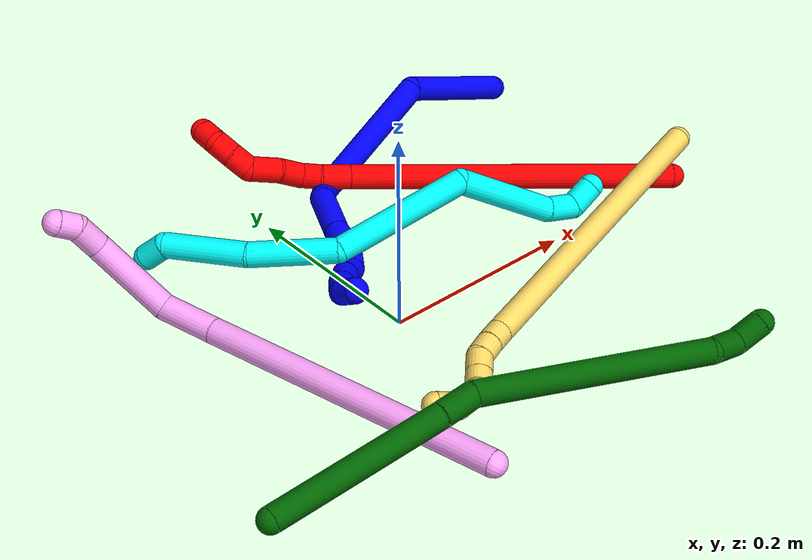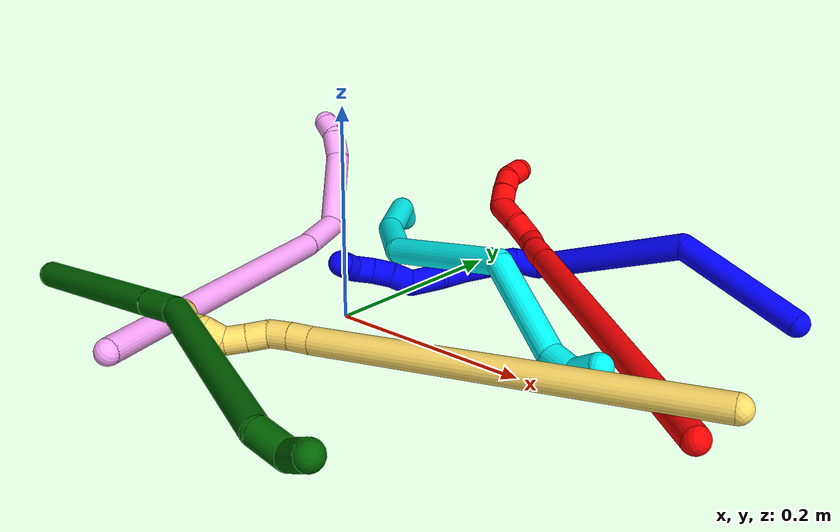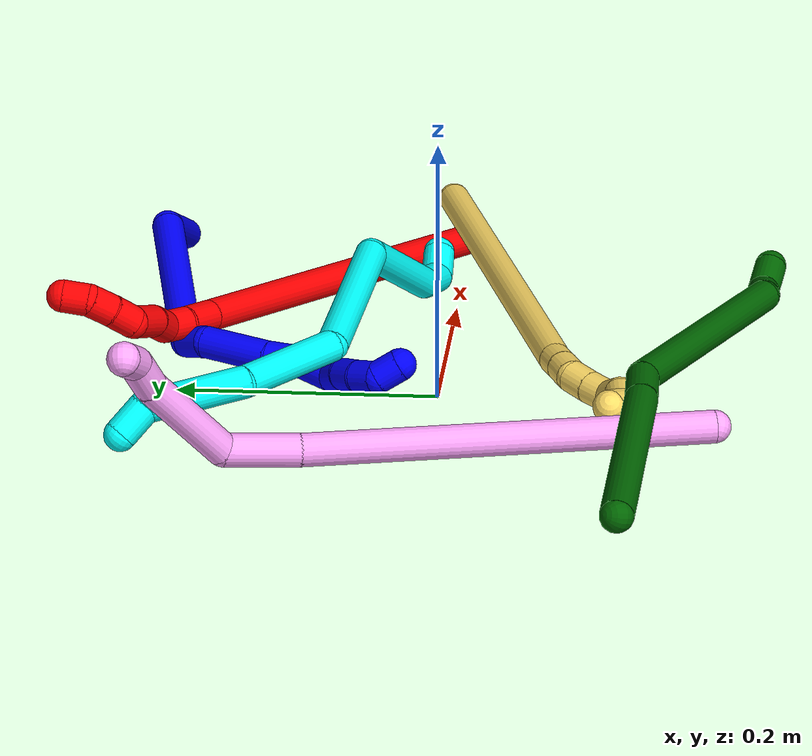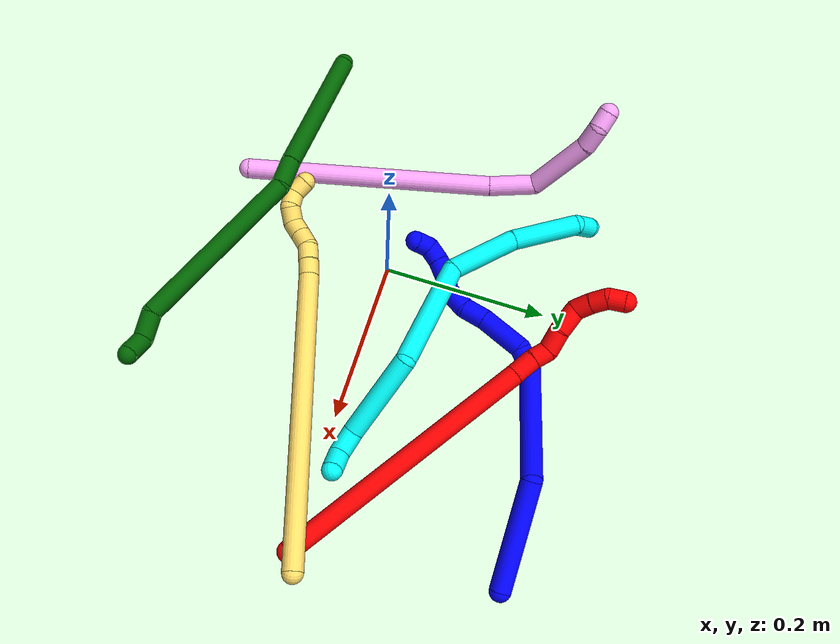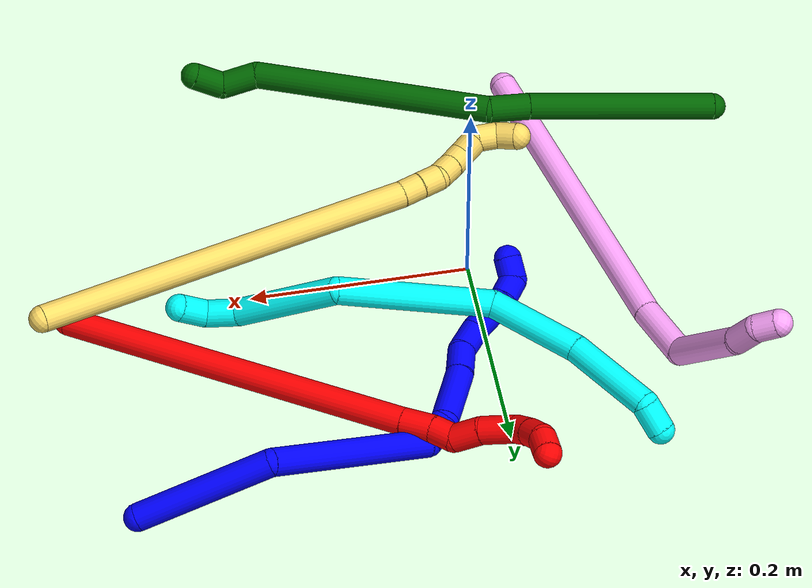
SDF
<sdf version="1.7">
 <world name="default">
  <plugin name="TubeGeneratorPlugin" filename="libtube_generator_plugin.so"/>
  <model name="photoneo_s_sensor">
   <static>1</static>
   <pose>0 0 2 1.57079 1.57079 3.14159</pose>
   <link name="link">
    <inertial><mass>0.1</mass></inertial>
    <sensor name="sensor" type="depth">
     <update_rate>30</update_rate>
     <camera>
      <horizontal_fov>1.22</horizontal_fov>
      <image><width>1920</width><height>1200</height><format>B8G8R8</format></image>
      <clip><near>0.1</near><far>4</far></clip>
      <depth_camera><output>points</output></depth_camera>
     </camera>
     <plugin name="camera_plugin" filename="libgazebo_ros_depth_camera.so">
      <baseline>0.2</baseline>
      <alwaysOn>1</alwaysOn>
      <updateRate>0.0</updateRate>
      <cameraName>camera_ir</cameraName>
      <imageTopicName>/camera/color/image_raw</imageTopicName>
      <cameraInfoTopicName>/camera/color/camera_info</cameraInfoTopicName>
      <depthImageTopicName>/camera/depth/image_raw</depthImageTopicName>
      <depthImageCameraInfoTopicName>/camera/depth/camera_info</depthImageCameraInfoTopicName>
      <pointCloudTopicName>/camera/depth/points</pointCloudTopicName>
      <frameName>fr_optical</frameName>
      <pointCloudCutoff>0.1</pointCloudCutoff>
      <pointCloudCutoffMax>2.0</pointCloudCutoffMax>
      <distortionK1>0</distortionK1>
      <distortionK2>0</distortionK2>
      <distortionK3>0</distortionK3>
      <distortionT1>0</distortionT1>
      <distortionT2>0</distortionT2>
      <CxPrime>0</CxPrime>
      <Cx>0</Cx>
      <Cy>0</Cy>
      <focalLength>0</focalLength>
      <hackBaseline>0</hackBaseline>
     </plugin>
    </sensor>
   </link>
  </model>
  <gravity>0 0 -9.8</gravity>
  <magnetic_field>6e-06 2.3e-05 -4.2e-05</magnetic_field>
  <atmosphere type="adiabatic"/>
  <physics name="default_physics" default="0" type="ode">
   <max_step_size>0.003</max_step_size>
   <real_time_factor>1</real_time_factor>
   <real_time_update_rate>1000</real_time_update_rate>
   <max_contacts>10000</max_contacts>
   <ode>
    <solver>
     <type>quick</type>
     <iters>100</iters>
     <sor>1.3</sor>
     <use_dynamic_moi_rescaling>0</use_dynamic_moi_rescaling>
    </solver>
    <constraints>
     <contact_max_correcting_vel>0</contact_max_correcting_vel>
     <contact_surface_layer>0.001</contact_surface_layer>
     <cfm>0</cfm>
     <erp>0.2</erp>
    </constraints>
   </ode>
  </physics>
  <scene><ambient>0.4 0.4 0.4 1</ambient><background>0.7 0.7 0.7 1</background><shadows>0</shadows></scene>
  <audio><device>default</device></audio>
  <spherical_coordinates>
   <surface_model>EARTH_WGS84</surface_model>
   <latitude_deg>0</latitude_deg>
   <longitude_deg>0</longitude_deg>
   <elevation>0</elevation>
   <heading_deg>0</heading_deg>
  </spherical_coordinates>
  <model name="bin">
   <static>1</static>
   <link name="bottom">
    <collision name="collision-bottom">
     <pose>0 0 -0.01 0 -0 0</pose>
     <geometry><box><size>0.8 0.6 0.02</size></box></geometry>
     <surface>
      <friction><ode><mu>100</mu><mu2>100</mu2></ode></friction>
      <contact><collide_bitmask>65535</collide_bitmask></contact>
     </surface>
    </collision>
   </link>
   <link name="west_wall">
    <collision name="collision-west_wall">
     <pose>-0.41 0 0.1 0 -0 0</pose>
     <geometry><box><size>0.02 0.6 0.2</size></box></geometry>
     <surface>
      <friction><ode><mu>100</mu><mu2>100</mu2></ode></friction>
      <contact><collide_bitmask>65535</collide_bitmask></contact>
     </surface>
    </collision>
   </link>
   <link name="east_wall">
    <collision name="collision-east_wall">
     <pose>0.41 0 0.1 0 -0 0</pose>
     <geometry><box><size>0.02 0.6 0.2</size></box></geometry>
     <surface>
      <friction><ode><mu>100</mu><mu2>100</mu2></ode></friction>
      <contact><collide_bitmask>65535</collide_bitmask></contact>
     </surface>
    </collision>
   </link>
   <link name="south_wall">
    <collision name="collision-south_wall">
     <pose>0 -0.31 0.1 0 -0 0</pose>
     <geometry><box><size>0.8 0.02 0.2</size></box></geometry>
     <surface>
      <friction><ode><mu>100</mu><mu2>100</mu2></ode></friction>
      <contact><collide_bitmask>65535</collide_bitmask></contact>
     </surface>
    </collision>
   </link>
   <link name="north_wall">
    <collision name="collision-north_wall">
     <pose>0 0.31 0.1 0 -0 0</pose>
     <geometry><box><size>0.8 0.02 0.2</size></box></geometry>
     <surface>
      <friction><ode><mu>100</mu><mu2>100</mu2></ode></friction>
      <contact><collide_bitmask>65535</collide_bitmask></contact>
     </surface>
    </collision>
   </link>
  </model>
  <model name="1">
   <static>0</static>
   <link name="1">
    <collision name="collision-cylinder-e_1_1_4">
     <pose>-0.056295 -0.003179 -0.028383 3.03003 -1.1013 -2.96021</pose>
     <geometry><cylinder><radius>0.0125</radius><length>0.12625</length></cylinder></geometry>
     <surface>
      <friction><ode><mu>1.16</mu><mu2>1.16</mu2><slip1>0</slip1><slip2>0</slip2></ode></friction>
      <contact><ode><kp>1e+06</kp><kd>1</kd><max_vel>0</max_vel><min_depth>0.001</min_depth></ode></contact>
     </surface>
    </collision>
    <visual name="visual-cylinder-e_1_1_4">
     <pose>-0.056295 -0.003179 -0.028383 3.03003 -1.1013 -2.96021</pose>
     <geometry><cylinder><radius>0.0125</radius><length>0.12625</length></cylinder></geometry>
     <material><ambient>0 0 1 1</ambient></material>
    </visual>
    <collision name="collision-cylinder-e_2_4_5">
     <pose>-0.146343 0.017499 -0.121267 -2.78732 -0.456263 1.82794</pose>
     <geometry><cylinder><radius>0.0125</radius><length>0.153219</length></cylinder></geometry>
     <surface>
      <friction><ode><mu>1.16</mu><mu2>1.16</mu2><slip1>0</slip1><slip2>0</slip2></ode></friction>
      <contact><ode><kp>1e+06</kp><kd>1</kd><max_vel>0</max_vel><min_depth>0.001</min_depth></ode></contact>
     </surface>
    </collision>
    <visual name="visual-cylinder-e_2_4_5">
     <pose>-0.146343 0.017499 -0.121267 -2.78732 -0.456263 1.82794</pose>
     <geometry><cylinder><radius>0.0125</radius><length>0.153219</length></cylinder></geometry>
     <material><ambient>0 0 1 1</ambient></material>
    </visual>
    <collision name="collision-cylinder-e_3_5_6">
     <pose>-0.185568 0.035415 -0.196338 2.62947 -0.423912 -1.37595</pose>
     <geometry><cylinder><radius>0.0125</radius><length>0.026604</length></cylinder></geometry>
     <surface>
      <friction><ode><mu>1.16</mu><mu2>1.16</mu2><slip1>0</slip1><slip2>0</slip2></ode></friction>
      <contact><ode><kp>1e+06</kp><kd>1</kd><max_vel>0</max_vel><min_depth>0.001</min_depth></ode></contact>
     </surface>
    </collision>
    <visual name="visual-cylinder-e_3_5_6">
     <pose>-0.185568 0.035415 -0.196338 2.62947 -0.423912 -1.37595</pose>
     <geometry><cylinder><radius>0.0125</radius><length>0.026604</length></cylinder></geometry>
     <material><ambient>0 0 1 1</ambient></material>
    </visual>
    <collision name="collision-cylinder-e_4_6_7">
     <pose>-0.189748 0.017066 -0.231739 2.6782 0.046511 0.196537</pose>
     <geometry><cylinder><radius>0.0125</radius><length>0.055578</length></cylinder></geometry>
     <surface>
      <friction><ode><mu>1.16</mu><mu2>1.16</mu2><slip1>0</slip1><slip2>0</slip2></ode></friction>
      <contact><ode><kp>1e+06</kp><kd>1</kd><max_vel>0</max_vel><min_depth>0.001</min_depth></ode></contact>
     </surface>
    </collision>
    <visual name="visual-cylinder-e_4_6_7">
     <pose>-0.189748 0.017066 -0.231739 2.6782 0.046511 0.196537</pose>
     <geometry><cylinder><radius>0.0125</radius><length>0.055578</length></cylinder></geometry>
     <material><ambient>0 0 1 1</ambient></material>
    </visual>
    <collision name="collision-cylinder-e_5_7_8">
     <pose>-0.185903 -0.002689 -0.268133 2.57554 0.184281 0.615253</pose>
     <geometry><cylinder><radius>0.0125</radius><length>0.02787</length></cylinder></geometry>
     <surface>
      <friction><ode><mu>1.16</mu><mu2>1.16</mu2><slip1>0</slip1><slip2>0</slip2></ode></friction>
      <contact><ode><kp>1e+06</kp><kd>1</kd><max_vel>0</max_vel><min_depth>0.001</min_depth></ode></contact>
     </surface>
    </collision>
    <visual name="visual-cylinder-e_5_7_8">
     <pose>-0.185903 -0.002689 -0.268133 2.57554 0.184281 0.615253</pose>
     <geometry><cylinder><radius>0.0125</radius><length>0.02787</length></cylinder></geometry>
     <material><ambient>0 0 1 1</ambient></material>
    </visual>
    <collision name="collision-cylinder-e_6_8_9">
     <pose>-0.183976 -0.014377 -0.294268 2.85207 -0.041217 -0.280913</pose>
     <geometry><cylinder><radius>0.0125</radius><length>0.030438</length></cylinder></geometry>
     <surface>
      <friction><ode><mu>1.16</mu><mu2>1.16</mu2><slip1>0</slip1><slip2>0</slip2></ode></friction>
      <contact><ode><kp>1e+06</kp><kd>1</kd><max_vel>0</max_vel><min_depth>0.001</min_depth></ode></contact>
     </surface>
    </collision>
    <visual name="visual-cylinder-e_6_8_9">
     <pose>-0.183976 -0.014377 -0.294268 2.85207 -0.041217 -0.280913</pose>
     <geometry><cylinder><radius>0.0125</radius><length>0.030438</length></cylinder></geometry>
     <material><ambient>0 0 1 1</ambient></material>
    </visual>
    <collision name="collision-cylinder-e_7_9_10">
     <pose>-0.190668 -0.022675 -0.315762 2.62217 -0.650338 -1.80665</pose>
     <geometry><cylinder><radius>0.0125</radius><length>0.020035</length></cylinder></geometry>
     <surface>
      <friction><ode><mu>1.16</mu><mu2>1.16</mu2><slip1>0</slip1><slip2>0</slip2></ode></friction>
      <contact><ode><kp>1e+06</kp><kd>1</kd><max_vel>0</max_vel><min_depth>0.001</min_depth></ode></contact>
     </surface>
    </collision>
    <visual name="visual-cylinder-e_7_9_10">
     <pose>-0.190668 -0.022675 -0.315762 2.62217 -0.650338 -1.80665</pose>
     <geometry><cylinder><radius>0.0125</radius><length>0.020035</length></cylinder></geometry>
     <material><ambient>0 0 1 1</ambient></material>
    </visual>
    <collision name="collision-cylinder-e_8_10_11">
     <pose>-0.201125 -0.030456 -0.330814 2.7021 -0.454577 -1.60569</pose>
     <geometry><cylinder><radius>0.0125</radius><length>0.020001</length></cylinder></geometry>
     <surface>
      <friction><ode><mu>1.16</mu><mu2>1.16</mu2><slip1>0</slip1><slip2>0</slip2></ode></friction>
      <contact><ode><kp>1e+06</kp><kd>1</kd><max_vel>0</max_vel><min_depth>0.001</min_depth></ode></contact>
     </surface>
    </collision>
    <visual name="visual-cylinder-e_8_10_11">
     <pose>-0.201125 -0.030456 -0.330814 2.7021 -0.454577 -1.60569</pose>
     <geometry><cylinder><radius>0.0125</radius><length>0.020001</length></cylinder></geometry>
     <material><ambient>0 0 1 1</ambient></material>
    </visual>
    <collision name="collision-cylinder-e_9_11_12">
     <pose>-0.208165 -0.039232 -0.347221 2.60229 -0.268078 -0.907838</pose>
     <geometry><cylinder><radius>0.0125</radius><length>0.020005</length></cylinder></geometry>
     <surface>
      <friction><ode><mu>1.16</mu><mu2>1.16</mu2><slip1>0</slip1><slip2>0</slip2></ode></friction>
      <contact><ode><kp>1e+06</kp><kd>1</kd><max_vel>0</max_vel><min_depth>0.001</min_depth></ode></contact>
     </surface>
    </collision>
    <visual name="visual-cylinder-e_9_11_12">
     <pose>-0.208165 -0.039232 -0.347221 2.60229 -0.268078 -0.907838</pose>
     <geometry><cylinder><radius>0.0125</radius><length>0.020005</length></cylinder></geometry>
     <material><ambient>0 0 1 1</ambient></material>
    </visual>
    <collision name="collision-cylinder-e_10_12_2">
     <pose>-0.209919 -0.053595 -0.358761 1.90461 0.089658 0.125907</pose>
     <geometry><cylinder><radius>0.0125</radius><length>0.02</length></cylinder></geometry>
     <surface>
      <friction><ode><mu>1.16</mu><mu2>1.16</mu2><slip1>0</slip1><slip2>0</slip2></ode></friction>
      <contact><ode><kp>1e+06</kp><kd>1</kd><max_vel>0</max_vel><min_depth>0.001</min_depth></ode></contact>
     </surface>
    </collision>
    <visual name="visual-cylinder-e_10_12_2">
     <pose>-0.209919 -0.053595 -0.358761 1.90461 0.089658 0.125907</pose>
     <geometry><cylinder><radius>0.0125</radius><length>0.02</length></cylinder></geometry>
     <material><ambient>0 0 1 1</ambient></material>
    </visual>
    <collision name="collision-sphere-2">
     <pose>-0.209024 -0.063006 -0.362025 0 -0 0</pose>
     <geometry><sphere><radius>0.0125</radius></sphere></geometry>
     <surface>
      <friction><ode><mu>1.16</mu><mu2>1.16</mu2><slip1>0</slip1><slip2>0</slip2></ode></friction>
      <contact><ode><kp>1e+06</kp><kd>1</kd><max_vel>0</max_vel><min_depth>0.001</min_depth></ode></contact>
     </surface>
    </collision>
    <visual name="visual-sphere-2">
     <pose>-0.209024 -0.063006 -0.362025 0 -0 0</pose>
     <geometry><sphere><radius>0.0125</radius></sphere></geometry>
     <material><ambient>0 0 1 1</ambient></material>
    </visual>
    <collision name="collision-sphere-12">
     <pose>-0.210815 -0.044185 -0.355498 0 -0 0</pose>
     <geometry><sphere><radius>0.0125</radius></sphere></geometry>
     <surface>
      <friction><ode><mu>1.16</mu><mu2>1.16</mu2><slip1>0</slip1><slip2>0</slip2></ode></friction>
      <contact><ode><kp>1e+06</kp><kd>1</kd><max_vel>0</max_vel><min_depth>0.001</min_depth></ode></contact>
     </surface>
    </collision>
    <visual name="visual-sphere-12">
     <pose>-0.210815 -0.044185 -0.355498 0 -0 0</pose>
     <geometry><sphere><radius>0.0125</radius></sphere></geometry>
     <material><ambient>0 0 1 1</ambient></material>
    </visual>
    <collision name="collision-sphere-11">
     <pose>-0.205516 -0.034279 -0.338945 0 -0 0</pose>
     <geometry><sphere><radius>0.0125</radius></sphere></geometry>
     <surface>
      <friction><ode><mu>1.16</mu><mu2>1.16</mu2><slip1>0</slip1><slip2>0</slip2></ode></friction>
      <contact><ode><kp>1e+06</kp><kd>1</kd><max_vel>0</max_vel><min_depth>0.001</min_depth></ode></contact>
     </surface>
    </collision>
    <visual name="visual-sphere-11">
     <pose>-0.205516 -0.034279 -0.338945 0 -0 0</pose>
     <geometry><sphere><radius>0.0125</radius></sphere></geometry>
     <material><ambient>0 0 1 1</ambient></material>
    </visual>
    <collision name="collision-sphere-10">
     <pose>-0.196734 -0.026633 -0.322683 0 -0 0</pose>
     <geometry><sphere><radius>0.0125</radius></sphere></geometry>
     <surface>
      <friction><ode><mu>1.16</mu><mu2>1.16</mu2><slip1>0</slip1><slip2>0</slip2></ode></friction>
      <contact><ode><kp>1e+06</kp><kd>1</kd><max_vel>0</max_vel><min_depth>0.001</min_depth></ode></contact>
     </surface>
    </collision>
    <visual name="visual-sphere-10">
     <pose>-0.196734 -0.026633 -0.322683 0 -0 0</pose>
     <geometry><sphere><radius>0.0125</radius></sphere></geometry>
     <material><ambient>0 0 1 1</ambient></material>
    </visual>
    <collision name="collision-sphere-9">
     <pose>-0.184603 -0.018718 -0.308841 0 -0 0</pose>
     <geometry><sphere><radius>0.0125</radius></sphere></geometry>
     <surface>
      <friction><ode><mu>1.16</mu><mu2>1.16</mu2><slip1>0</slip1><slip2>0</slip2></ode></friction>
      <contact><ode><kp>1e+06</kp><kd>1</kd><max_vel>0</max_vel><min_depth>0.001</min_depth></ode></contact>
     </surface>
    </collision>
    <visual name="visual-sphere-9">
     <pose>-0.184603 -0.018718 -0.308841 0 -0 0</pose>
     <geometry><sphere><radius>0.0125</radius></sphere></geometry>
     <material><ambient>0 0 1 1</ambient></material>
    </visual>
    <collision name="collision-sphere-4">
     <pose>-0.112589 -0.006359 -0.056765 0 -0 0</pose>
     <geometry><sphere><radius>0.0125</radius></sphere></geometry>
     <surface>
      <friction><ode><mu>1.16</mu><mu2>1.16</mu2><slip1>0</slip1><slip2>0</slip2></ode></friction>
      <contact><ode><kp>1e+06</kp><kd>1</kd><max_vel>0</max_vel><min_depth>0.001</min_depth></ode></contact>
     </surface>
    </collision>
    <visual name="visual-sphere-4">
     <pose>-0.112589 -0.006359 -0.056765 0 -0 0</pose>
     <geometry><sphere><radius>0.0125</radius></sphere></geometry>
     <material><ambient>0 0 1 1</ambient></material>
    </visual>
    <collision name="collision-sphere-1">
     <geometry><sphere><radius>0.0125</radius></sphere></geometry>
     <surface>
      <friction><ode><mu>1.16</mu><mu2>1.16</mu2><slip1>0</slip1><slip2>0</slip2></ode></friction>
      <contact><ode><kp>1e+06</kp><kd>1</kd><max_vel>0</max_vel><min_depth>0.001</min_depth></ode></contact>
     </surface>
    </collision>
    <visual name="visual-sphere-1">
     <geometry><sphere><radius>0.0125</radius></sphere></geometry>
     <material><ambient>0 0 1 1</ambient></material>
    </visual>
    <collision name="collision-sphere-8">
     <pose>-0.183349 -0.010035 -0.279695 0 -0 0</pose>
     <geometry><sphere><radius>0.0125</radius></sphere></geometry>
     <surface>
      <friction><ode><mu>1.16</mu><mu2>1.16</mu2><slip1>0</slip1><slip2>0</slip2></ode></friction>
      <contact><ode><kp>1e+06</kp><kd>1</kd><max_vel>0</max_vel><min_depth>0.001</min_depth></ode></contact>
     </surface>
    </collision>
    <visual name="visual-sphere-8">
     <pose>-0.183349 -0.010035 -0.279695 0 -0 0</pose>
     <geometry><sphere><radius>0.0125</radius></sphere></geometry>
     <material><ambient>0 0 1 1</ambient></material>
    </visual>
    <collision name="collision-sphere-5">
     <pose>-0.180097 0.041357 -0.185769 0 -0 0</pose>
     <geometry><sphere><radius>0.0125</radius></sphere></geometry>
     <surface>
      <friction><ode><mu>1.16</mu><mu2>1.16</mu2><slip1>0</slip1><slip2>0</slip2></ode></friction>
      <contact><ode><kp>1e+06</kp><kd>1</kd><max_vel>0</max_vel><min_depth>0.001</min_depth></ode></contact>
     </surface>
    </collision>
    <visual name="visual-sphere-5">
     <pose>-0.180097 0.041357 -0.185769 0 -0 0</pose>
     <geometry><sphere><radius>0.0125</radius></sphere></geometry>
     <material><ambient>0 0 1 1</ambient></material>
    </visual>
    <collision name="collision-sphere-6">
     <pose>-0.19104 0.029474 -0.206907 0 -0 0</pose>
     <geometry><sphere><radius>0.0125</radius></sphere></geometry>
     <surface>
      <friction><ode><mu>1.16</mu><mu2>1.16</mu2><slip1>0</slip1><slip2>0</slip2></ode></friction>
      <contact><ode><kp>1e+06</kp><kd>1</kd><max_vel>0</max_vel><min_depth>0.001</min_depth></ode></contact>
     </surface>
    </collision>
    <visual name="visual-sphere-6">
     <pose>-0.19104 0.029474 -0.206907 0 -0 0</pose>
     <geometry><sphere><radius>0.0125</radius></sphere></geometry>
     <material><ambient>0 0 1 1</ambient></material>
    </visual>
    <collision name="collision-sphere-7">
     <pose>-0.188456 0.004658 -0.256571 0 -0 0</pose>
     <geometry><sphere><radius>0.0125</radius></sphere></geometry>
     <surface>
      <friction><ode><mu>1.16</mu><mu2>1.16</mu2><slip1>0</slip1><slip2>0</slip2></ode></friction>
      <contact><ode><kp>1e+06</kp><kd>1</kd><max_vel>0</max_vel><min_depth>0.001</min_depth></ode></contact>
     </surface>
    </collision>
    <visual name="visual-sphere-7">
     <pose>-0.188456 0.004658 -0.256571 0 -0 0</pose>
     <geometry><sphere><radius>0.0125</radius></sphere></geometry>
     <material><ambient>0 0 1 1</ambient></material>
    </visual>
    <inertial>
     <pose>-0.143998 0.001475 -0.167522 0 -0 0</pose>
     <mass>0.5</mass>
     <inertia>
      <ixx>0.000111</ixx>
      <ixy>0</ixy>
      <ixz>0</ixz>
      <iyy>0.000515</iyy>
      <iyz>0</iyz>
      <izz>0.00019</izz>
     </inertia>
    </inertial>
   </link>
   <pose>0.334025 0.237598 0.011842 -1.08935 0.599085 -0.453098</pose>
  </model>
  <model name="2">
   <static>0</static>
   <link name="2">
    <collision name="collision-cylinder-e_1_1_4">
     <pose>-0.103328 0.045001 -0.120714 -2.78476 -0.675993 2.19351</pose>
     <geometry><cylinder><radius>0.0125</radius><length>0.330296</length></cylinder></geometry>
     <surface>
      <friction><ode><mu>1.16</mu><mu2>1.16</mu2><slip1>0</slip1><slip2>0</slip2></ode></friction>
      <contact><ode><kp>1e+06</kp><kd>1</kd><max_vel>0</max_vel><min_depth>0.001</min_depth></ode></contact>
     </surface>
    </collision>
    <visual name="visual-cylinder-e_1_1_4">
     <pose>-0.103328 0.045001 -0.120714 -2.78476 -0.675993 2.19351</pose>
     <geometry><cylinder><radius>0.0125</radius><length>0.330296</length></cylinder></geometry>
     <material><ambient>1 0 0 1</ambient></material>
    </visual>
    <collision name="collision-cylinder-e_2_4_5">
     <pose>-0.215742 0.0933 -0.251823 -2.83428 -0.694612 2.33301</pose>
     <geometry><cylinder><radius>0.0125</radius><length>0.028388</length></cylinder></geometry>
     <surface>
      <friction><ode><mu>1.16</mu><mu2>1.16</mu2><slip1>0</slip1><slip2>0</slip2></ode></friction>
      <contact><ode><kp>1e+06</kp><kd>1</kd><max_vel>0</max_vel><min_depth>0.001</min_depth></ode></contact>
     </surface>
    </collision>
    <visual name="visual-cylinder-e_2_4_5">
     <pose>-0.215742 0.0933 -0.251823 -2.83428 -0.694612 2.33301</pose>
     <geometry><cylinder><radius>0.0125</radius><length>0.028388</length></cylinder></geometry>
     <material><ambient>1 0 0 1</ambient></material>
    </visual>
    <collision name="collision-cylinder-e_3_5_6">
     <pose>-0.231455 0.100945 -0.269281 -2.59003 -0.674217 1.78308</pose>
     <geometry><cylinder><radius>0.0125</radius><length>0.021231</length></cylinder></geometry>
     <surface>
      <friction><ode><mu>1.16</mu><mu2>1.16</mu2><slip1>0</slip1><slip2>0</slip2></ode></friction>
      <contact><ode><kp>1e+06</kp><kd>1</kd><max_vel>0</max_vel><min_depth>0.001</min_depth></ode></contact>
     </surface>
    </collision>
    <visual name="visual-cylinder-e_3_5_6">
     <pose>-0.231455 0.100945 -0.269281 -2.59003 -0.674217 1.78308</pose>
     <geometry><cylinder><radius>0.0125</radius><length>0.021231</length></cylinder></geometry>
     <material><ambient>1 0 0 1</ambient></material>
    </visual>
    <collision name="collision-cylinder-e_4_6_7">
     <pose>-0.249355 0.102955 -0.283313 2.81826 -0.993016 -2.5568</pose>
     <geometry><cylinder><radius>0.0125</radius><length>0.026915</length></cylinder></geometry>
     <surface>
      <friction><ode><mu>1.16</mu><mu2>1.16</mu2><slip1>0</slip1><slip2>0</slip2></ode></friction>
      <contact><ode><kp>1e+06</kp><kd>1</kd><max_vel>0</max_vel><min_depth>0.001</min_depth></ode></contact>
     </surface>
    </collision>
    <visual name="visual-cylinder-e_4_6_7">
     <pose>-0.249355 0.102955 -0.283313 2.81826 -0.993016 -2.5568</pose>
     <geometry><cylinder><radius>0.0125</radius><length>0.026915</length></cylinder></geometry>
     <material><ambient>1 0 0 1</ambient></material>
    </visual>
    <collision name="collision-cylinder-e_5_7_8">
     <pose>-0.272357 0.100457 -0.300821 3.12614 -0.83873 -3.10694</pose>
     <geometry><cylinder><radius>0.0125</radius><length>0.031538</length></cylinder></geometry>
     <surface>
      <friction><ode><mu>1.16</mu><mu2>1.16</mu2><slip1>0</slip1><slip2>0</slip2></ode></friction>
      <contact><ode><kp>1e+06</kp><kd>1</kd><max_vel>0</max_vel><min_depth>0.001</min_depth></ode></contact>
     </surface>
    </collision>
    <visual name="visual-cylinder-e_5_7_8">
     <pose>-0.272357 0.100457 -0.300821 3.12614 -0.83873 -3.10694</pose>
     <geometry><cylinder><radius>0.0125</radius><length>0.031538</length></cylinder></geometry>
     <material><ambient>1 0 0 1</ambient></material>
    </visual>
    <collision name="collision-cylinder-e_6_8_9">
     <pose>-0.293923 0.104355 -0.312892 -1.93158 -1.15527 1.51168</pose>
     <geometry><cylinder><radius>0.0125</radius><length>0.021504</length></cylinder></geometry>
     <surface>
      <friction><ode><mu>1.16</mu><mu2>1.16</mu2><slip1>0</slip1><slip2>0</slip2></ode></friction>
      <contact><ode><kp>1e+06</kp><kd>1</kd><max_vel>0</max_vel><min_depth>0.001</min_depth></ode></contact>
     </surface>
    </collision>
    <visual name="visual-cylinder-e_6_8_9">
     <pose>-0.293923 0.104355 -0.312892 -1.93158 -1.15527 1.51168</pose>
     <geometry><cylinder><radius>0.0125</radius><length>0.021504</length></cylinder></geometry>
     <material><ambient>1 0 0 1</ambient></material>
    </visual>
    <collision name="collision-cylinder-e_7_9_10">
     <pose>-0.312451 0.11326 -0.315566 -1.80229 -1.05068 1.26403</pose>
     <geometry><cylinder><radius>0.0125</radius><length>0.020031</length></cylinder></geometry>
     <surface>
      <friction><ode><mu>1.16</mu><mu2>1.16</mu2><slip1>0</slip1><slip2>0</slip2></ode></friction>
      <contact><ode><kp>1e+06</kp><kd>1</kd><max_vel>0</max_vel><min_depth>0.001</min_depth></ode></contact>
     </surface>
    </collision>
    <visual name="visual-cylinder-e_7_9_10">
     <pose>-0.312451 0.11326 -0.315566 -1.80229 -1.05068 1.26403</pose>
     <geometry><cylinder><radius>0.0125</radius><length>0.020031</length></cylinder></geometry>
     <material><ambient>1 0 0 1</ambient></material>
    </visual>
    <collision name="collision-cylinder-e_8_10_2">
     <pose>-0.326342 0.126692 -0.317166 -1.62407 -0.543865 0.57208</pose>
     <geometry><cylinder><radius>0.0125</radius><length>0.020097</length></cylinder></geometry>
     <surface>
      <friction><ode><mu>1.16</mu><mu2>1.16</mu2><slip1>0</slip1><slip2>0</slip2></ode></friction>
      <contact><ode><kp>1e+06</kp><kd>1</kd><max_vel>0</max_vel><min_depth>0.001</min_depth></ode></contact>
     </surface>
    </collision>
    <visual name="visual-cylinder-e_8_10_2">
     <pose>-0.326342 0.126692 -0.317166 -1.62407 -0.543865 0.57208</pose>
     <geometry><cylinder><radius>0.0125</radius><length>0.020097</length></cylinder></geometry>
     <material><ambient>1 0 0 1</ambient></material>
    </visual>
    <collision name="collision-sphere-2">
     <pose>-0.331541 0.135278 -0.317624 0 -0 0</pose>
     <geometry><sphere><radius>0.0125</radius></sphere></geometry>
     <surface>
      <friction><ode><mu>1.16</mu><mu2>1.16</mu2><slip1>0</slip1><slip2>0</slip2></ode></friction>
      <contact><ode><kp>1e+06</kp><kd>1</kd><max_vel>0</max_vel><min_depth>0.001</min_depth></ode></contact>
     </surface>
    </collision>
    <visual name="visual-sphere-2">
     <pose>-0.331541 0.135278 -0.317624 0 -0 0</pose>
     <geometry><sphere><radius>0.0125</radius></sphere></geometry>
     <material><ambient>1 0 0 1</ambient></material>
    </visual>
    <collision name="collision-sphere-10">
     <pose>-0.321142 0.118105 -0.316708 0 -0 0</pose>
     <geometry><sphere><radius>0.0125</radius></sphere></geometry>
     <surface>
      <friction><ode><mu>1.16</mu><mu2>1.16</mu2><slip1>0</slip1><slip2>0</slip2></ode></friction>
      <contact><ode><kp>1e+06</kp><kd>1</kd><max_vel>0</max_vel><min_depth>0.001</min_depth></ode></contact>
     </surface>
    </collision>
    <visual name="visual-sphere-10">
     <pose>-0.321142 0.118105 -0.316708 0 -0 0</pose>
     <geometry><sphere><radius>0.0125</radius></sphere></geometry>
     <material><ambient>1 0 0 1</ambient></material>
    </visual>
    <collision name="collision-sphere-9">
     <pose>-0.30376 0.108416 -0.314424 0 -0 0</pose>
     <geometry><sphere><radius>0.0125</radius></sphere></geometry>
     <surface>
      <friction><ode><mu>1.16</mu><mu2>1.16</mu2><slip1>0</slip1><slip2>0</slip2></ode></friction>
      <contact><ode><kp>1e+06</kp><kd>1</kd><max_vel>0</max_vel><min_depth>0.001</min_depth></ode></contact>
     </surface>
    </collision>
    <visual name="visual-sphere-9">
     <pose>-0.30376 0.108416 -0.314424 0 -0 0</pose>
     <geometry><sphere><radius>0.0125</radius></sphere></geometry>
     <material><ambient>1 0 0 1</ambient></material>
    </visual>
    <collision name="collision-sphere-4">
     <pose>-0.206657 0.090001 -0.241429 0 -0 0</pose>
     <geometry><sphere><radius>0.0125</radius></sphere></geometry>
     <surface>
      <friction><ode><mu>1.16</mu><mu2>1.16</mu2><slip1>0</slip1><slip2>0</slip2></ode></friction>
      <contact><ode><kp>1e+06</kp><kd>1</kd><max_vel>0</max_vel><min_depth>0.001</min_depth></ode></contact>
     </surface>
    </collision>
    <visual name="visual-sphere-4">
     <pose>-0.206657 0.090001 -0.241429 0 -0 0</pose>
     <geometry><sphere><radius>0.0125</radius></sphere></geometry>
     <material><ambient>1 0 0 1</ambient></material>
    </visual>
    <collision name="collision-sphere-1">
     <geometry><sphere><radius>0.0125</radius></sphere></geometry>
     <surface>
      <friction><ode><mu>1.16</mu><mu2>1.16</mu2><slip1>0</slip1><slip2>0</slip2></ode></friction>
      <contact><ode><kp>1e+06</kp><kd>1</kd><max_vel>0</max_vel><min_depth>0.001</min_depth></ode></contact>
     </surface>
    </collision>
    <visual name="visual-sphere-1">
     <geometry><sphere><radius>0.0125</radius></sphere></geometry>
     <material><ambient>1 0 0 1</ambient></material>
    </visual>
    <collision name="collision-sphere-8">
     <pose>-0.284086 0.100294 -0.31136 0 -0 0</pose>
     <geometry><sphere><radius>0.0125</radius></sphere></geometry>
     <surface>
      <friction><ode><mu>1.16</mu><mu2>1.16</mu2><slip1>0</slip1><slip2>0</slip2></ode></friction>
      <contact><ode><kp>1e+06</kp><kd>1</kd><max_vel>0</max_vel><min_depth>0.001</min_depth></ode></contact>
     </surface>
    </collision>
    <visual name="visual-sphere-8">
     <pose>-0.284086 0.100294 -0.31136 0 -0 0</pose>
     <geometry><sphere><radius>0.0125</radius></sphere></geometry>
     <material><ambient>1 0 0 1</ambient></material>
    </visual>
    <collision name="collision-sphere-5">
     <pose>-0.224828 0.096599 -0.262218 0 -0 0</pose>
     <geometry><sphere><radius>0.0125</radius></sphere></geometry>
     <surface>
      <friction><ode><mu>1.16</mu><mu2>1.16</mu2><slip1>0</slip1><slip2>0</slip2></ode></friction>
      <contact><ode><kp>1e+06</kp><kd>1</kd><max_vel>0</max_vel><min_depth>0.001</min_depth></ode></contact>
     </surface>
    </collision>
    <visual name="visual-sphere-5">
     <pose>-0.224828 0.096599 -0.262218 0 -0 0</pose>
     <geometry><sphere><radius>0.0125</radius></sphere></geometry>
     <material><ambient>1 0 0 1</ambient></material>
    </visual>
    <collision name="collision-sphere-6">
     <pose>-0.238082 0.10529 -0.276344 0 -0 0</pose>
     <geometry><sphere><radius>0.0125</radius></sphere></geometry>
     <surface>
      <friction><ode><mu>1.16</mu><mu2>1.16</mu2><slip1>0</slip1><slip2>0</slip2></ode></friction>
      <contact><ode><kp>1e+06</kp><kd>1</kd><max_vel>0</max_vel><min_depth>0.001</min_depth></ode></contact>
     </surface>
    </collision>
    <visual name="visual-sphere-6">
     <pose>-0.238082 0.10529 -0.276344 0 -0 0</pose>
     <geometry><sphere><radius>0.0125</radius></sphere></geometry>
     <material><ambient>1 0 0 1</ambient></material>
    </visual>
    <collision name="collision-sphere-7">
     <pose>-0.260628 0.10062 -0.290282 0 -0 0</pose>
     <geometry><sphere><radius>0.0125</radius></sphere></geometry>
     <surface>
      <friction><ode><mu>1.16</mu><mu2>1.16</mu2><slip1>0</slip1><slip2>0</slip2></ode></friction>
      <contact><ode><kp>1e+06</kp><kd>1</kd><max_vel>0</max_vel><min_depth>0.001</min_depth></ode></contact>
     </surface>
    </collision>
    <visual name="visual-sphere-7">
     <pose>-0.260628 0.10062 -0.290282 0 -0 0</pose>
     <geometry><sphere><radius>0.0125</radius></sphere></geometry>
     <material><ambient>1 0 0 1</ambient></material>
    </visual>
    <inertial>
     <pose>-0.159212 0.065307 -0.178547 0 -0 0</pose>
     <mass>0.5</mass>
     <inertia>
      <ixx>0.000513</ixx>
      <ixy>0</ixy>
      <ixz>0</ixz>
      <iyy>0.004121</iyy>
      <iyz>0</iyz>
      <izz>0.001048</izz>
     </inertia>
    </inertial>
   </link>
   <pose>0.365296 0.000187 0.003612 -0.536208 0.958757 -0.740402</pose>
  </model>
  <model name="3">
   <static>0</static>
   <link name="3">
    <collision name="collision-cylinder-e_1_1_4">
     <pose>-0.01121 0.007414 -0.001038 -1.70993 -0.982025 1.10244</pose>
     <geometry><cylinder><radius>0.0125</radius><length>0.02696</length></cylinder></geometry>
     <surface>
      <friction><ode><mu>1.16</mu><mu2>1.16</mu2><slip1>0</slip1><slip2>0</slip2></ode></friction>
      <contact><ode><kp>1e+06</kp><kd>1</kd><max_vel>0</max_vel><min_depth>0.001</min_depth></ode></contact>
     </surface>
    </collision>
    <visual name="visual-cylinder-e_1_1_4">
     <pose>-0.01121 0.007414 -0.001038 -1.70993 -0.982025 1.10244</pose>
     <geometry><cylinder><radius>0.0125</radius><length>0.02696</length></cylinder></geometry>
     <material><ambient>0.003922 1 0.996078 1</ambient></material>
    </visual>
    <collision name="collision-cylinder-e_2_4_5">
     <pose>-0.034882 0.017781 0.005745 -0.361118 -0.979867 0.194094</pose>
     <geometry><cylinder><radius>0.0125</radius><length>0.030013</length></cylinder></geometry>
     <surface>
      <friction><ode><mu>1.16</mu><mu2>1.16</mu2><slip1>0</slip1><slip2>0</slip2></ode></friction>
      <contact><ode><kp>1e+06</kp><kd>1</kd><max_vel>0</max_vel><min_depth>0.001</min_depth></ode></contact>
     </surface>
    </collision>
    <visual name="visual-cylinder-e_2_4_5">
     <pose>-0.034882 0.017781 0.005745 -0.361118 -0.979867 0.194094</pose>
     <geometry><cylinder><radius>0.0125</radius><length>0.030013</length></cylinder></geometry>
     <material><ambient>0.003922 1 0.996078 1</ambient></material>
    </visual>
    <collision name="collision-cylinder-e_3_5_6">
     <pose>-0.08203 0.017536 0.052698 0.081578 -0.723594 -0.030888</pose>
     <geometry><cylinder><radius>0.0125</radius><length>0.10478</length></cylinder></geometry>
     <surface>
      <friction><ode><mu>1.16</mu><mu2>1.16</mu2><slip1>0</slip1><slip2>0</slip2></ode></friction>
      <contact><ode><kp>1e+06</kp><kd>1</kd><max_vel>0</max_vel><min_depth>0.001</min_depth></ode></contact>
     </surface>
    </collision>
    <visual name="visual-cylinder-e_3_5_6">
     <pose>-0.08203 0.017536 0.052698 0.081578 -0.723594 -0.030888</pose>
     <geometry><cylinder><radius>0.0125</radius><length>0.10478</length></cylinder></geometry>
     <material><ambient>0.003922 1 0.996078 1</ambient></material>
    </visual>
    <collision name="collision-cylinder-e_4_6_7">
     <pose>-0.179328 0.042746 0.106942 -1.08193 -1.09606 0.702933</pose>
     <geometry><cylinder><radius>0.0125</radius><length>0.140793</length></cylinder></geometry>
     <surface>
      <friction><ode><mu>1.16</mu><mu2>1.16</mu2><slip1>0</slip1><slip2>0</slip2></ode></friction>
      <contact><ode><kp>1e+06</kp><kd>1</kd><max_vel>0</max_vel><min_depth>0.001</min_depth></ode></contact>
     </surface>
    </collision>
    <visual name="visual-cylinder-e_4_6_7">
     <pose>-0.179328 0.042746 0.106942 -1.08193 -1.09606 0.702933</pose>
     <geometry><cylinder><radius>0.0125</radius><length>0.140793</length></cylinder></geometry>
     <material><ambient>0.003922 1 0.996078 1</ambient></material>
    </visual>
    <collision name="collision-cylinder-e_5_7_8">
     <pose>-0.263339 0.096471 0.150003 -0.736 -0.516169 0.202857</pose>
     <geometry><cylinder><radius>0.0125</radius><length>0.086717</length></cylinder></geometry>
     <surface>
      <friction><ode><mu>1.16</mu><mu2>1.16</mu2><slip1>0</slip1><slip2>0</slip2></ode></friction>
      <contact><ode><kp>1e+06</kp><kd>1</kd><max_vel>0</max_vel><min_depth>0.001</min_depth></ode></contact>
     </surface>
    </collision>
    <visual name="visual-cylinder-e_5_7_8">
     <pose>-0.263339 0.096471 0.150003 -0.736 -0.516169 0.202857</pose>
     <geometry><cylinder><radius>0.0125</radius><length>0.086717</length></cylinder></geometry>
     <material><ambient>0.003922 1 0.996078 1</ambient></material>
    </visual>
    <collision name="collision-cylinder-e_6_8_9">
     <pose>-0.29644 0.147421 0.208675 -0.695341 -0.284493 0.103706</pose>
     <geometry><cylinder><radius>0.0125</radius><length>0.083377</length></cylinder></geometry>
     <surface>
      <friction><ode><mu>1.16</mu><mu2>1.16</mu2><slip1>0</slip1><slip2>0</slip2></ode></friction>
      <contact><ode><kp>1e+06</kp><kd>1</kd><max_vel>0</max_vel><min_depth>0.001</min_depth></ode></contact>
     </surface>
    </collision>
    <visual name="visual-cylinder-e_6_8_9">
     <pose>-0.29644 0.147421 0.208675 -0.695341 -0.284493 0.103706</pose>
     <geometry><cylinder><radius>0.0125</radius><length>0.083377</length></cylinder></geometry>
     <material><ambient>0.003922 1 0.996078 1</ambient></material>
    </visual>
    <collision name="collision-cylinder-e_7_9_2">
     <pose>-0.310829 0.18624 0.241863 -1.386 -0.197807 0.164423</pose>
     <geometry><cylinder><radius>0.0125</radius><length>0.02736</length></cylinder></geometry>
     <surface>
      <friction><ode><mu>1.16</mu><mu2>1.16</mu2><slip1>0</slip1><slip2>0</slip2></ode></friction>
      <contact><ode><kp>1e+06</kp><kd>1</kd><max_vel>0</max_vel><min_depth>0.001</min_depth></ode></contact>
     </surface>
    </collision>
    <visual name="visual-cylinder-e_7_9_2">
     <pose>-0.310829 0.18624 0.241863 -1.386 -0.197807 0.164423</pose>
     <geometry><cylinder><radius>0.0125</radius><length>0.02736</length></cylinder></geometry>
     <material><ambient>0.003922 1 0.996078 1</ambient></material>
    </visual>
    <collision name="collision-sphere-2">
     <pose>-0.313517 0.199425 0.244328 0 -0 0</pose>
     <geometry><sphere><radius>0.0125</radius></sphere></geometry>
     <surface>
      <friction><ode><mu>1.16</mu><mu2>1.16</mu2><slip1>0</slip1><slip2>0</slip2></ode></friction>
      <contact><ode><kp>1e+06</kp><kd>1</kd><max_vel>0</max_vel><min_depth>0.001</min_depth></ode></contact>
     </surface>
    </collision>
    <visual name="visual-sphere-2">
     <pose>-0.313517 0.199425 0.244328 0 -0 0</pose>
     <geometry><sphere><radius>0.0125</radius></sphere></geometry>
     <material><ambient>0.003922 1 0.996078 1</ambient></material>
    </visual>
    <collision name="collision-sphere-9">
     <pose>-0.30814 0.173055 0.239398 0 -0 0</pose>
     <geometry><sphere><radius>0.0125</radius></sphere></geometry>
     <surface>
      <friction><ode><mu>1.16</mu><mu2>1.16</mu2><slip1>0</slip1><slip2>0</slip2></ode></friction>
      <contact><ode><kp>1e+06</kp><kd>1</kd><max_vel>0</max_vel><min_depth>0.001</min_depth></ode></contact>
     </surface>
    </collision>
    <visual name="visual-sphere-9">
     <pose>-0.30814 0.173055 0.239398 0 -0 0</pose>
     <geometry><sphere><radius>0.0125</radius></sphere></geometry>
     <material><ambient>0.003922 1 0.996078 1</ambient></material>
    </visual>
    <collision name="collision-sphere-4">
     <pose>-0.02242 0.014827 -0.002076 0 -0 0</pose>
     <geometry><sphere><radius>0.0125</radius></sphere></geometry>
     <surface>
      <friction><ode><mu>1.16</mu><mu2>1.16</mu2><slip1>0</slip1><slip2>0</slip2></ode></friction>
      <contact><ode><kp>1e+06</kp><kd>1</kd><max_vel>0</max_vel><min_depth>0.001</min_depth></ode></contact>
     </surface>
    </collision>
    <visual name="visual-sphere-4">
     <pose>-0.02242 0.014827 -0.002076 0 -0 0</pose>
     <geometry><sphere><radius>0.0125</radius></sphere></geometry>
     <material><ambient>0.003922 1 0.996078 1</ambient></material>
    </visual>
    <collision name="collision-sphere-1">
     <geometry><sphere><radius>0.0125</radius></sphere></geometry>
     <surface>
      <friction><ode><mu>1.16</mu><mu2>1.16</mu2><slip1>0</slip1><slip2>0</slip2></ode></friction>
      <contact><ode><kp>1e+06</kp><kd>1</kd><max_vel>0</max_vel><min_depth>0.001</min_depth></ode></contact>
     </surface>
    </collision>
    <visual name="visual-sphere-1">
     <geometry><sphere><radius>0.0125</radius></sphere></geometry>
     <material><ambient>0.003922 1 0.996078 1</ambient></material>
    </visual>
    <collision name="collision-sphere-8">
     <pose>-0.284739 0.121787 0.177952 0 -0 0</pose>
     <geometry><sphere><radius>0.0125</radius></sphere></geometry>
     <surface>
      <friction><ode><mu>1.16</mu><mu2>1.16</mu2><slip1>0</slip1><slip2>0</slip2></ode></friction>
      <contact><ode><kp>1e+06</kp><kd>1</kd><max_vel>0</max_vel><min_depth>0.001</min_depth></ode></contact>
     </surface>
    </collision>
    <visual name="visual-sphere-8">
     <pose>-0.284739 0.121787 0.177952 0 -0 0</pose>
     <geometry><sphere><radius>0.0125</radius></sphere></geometry>
     <material><ambient>0.003922 1 0.996078 1</ambient></material>
    </visual>
    <collision name="collision-sphere-5">
     <pose>-0.047344 0.020735 0.013566 0 -0 0</pose>
     <geometry><sphere><radius>0.0125</radius></sphere></geometry>
     <surface>
      <friction><ode><mu>1.16</mu><mu2>1.16</mu2><slip1>0</slip1><slip2>0</slip2></ode></friction>
      <contact><ode><kp>1e+06</kp><kd>1</kd><max_vel>0</max_vel><min_depth>0.001</min_depth></ode></contact>
     </surface>
    </collision>
    <visual name="visual-sphere-5">
     <pose>-0.047344 0.020735 0.013566 0 -0 0</pose>
     <geometry><sphere><radius>0.0125</radius></sphere></geometry>
     <material><ambient>0.003922 1 0.996078 1</ambient></material>
    </visual>
    <collision name="collision-sphere-6">
     <pose>-0.116716 0.014336 0.09183 0 -0 0</pose>
     <geometry><sphere><radius>0.0125</radius></sphere></geometry>
     <surface>
      <friction><ode><mu>1.16</mu><mu2>1.16</mu2><slip1>0</slip1><slip2>0</slip2></ode></friction>
      <contact><ode><kp>1e+06</kp><kd>1</kd><max_vel>0</max_vel><min_depth>0.001</min_depth></ode></contact>
     </surface>
    </collision>
    <visual name="visual-sphere-6">
     <pose>-0.116716 0.014336 0.09183 0 -0 0</pose>
     <geometry><sphere><radius>0.0125</radius></sphere></geometry>
     <material><ambient>0.003922 1 0.996078 1</ambient></material>
    </visual>
    <collision name="collision-sphere-7">
     <pose>-0.241939 0.071156 0.122054 0 -0 0</pose>
     <geometry><sphere><radius>0.0125</radius></sphere></geometry>
     <surface>
      <friction><ode><mu>1.16</mu><mu2>1.16</mu2><slip1>0</slip1><slip2>0</slip2></ode></friction>
      <contact><ode><kp>1e+06</kp><kd>1</kd><max_vel>0</max_vel><min_depth>0.001</min_depth></ode></contact>
     </surface>
    </collision>
    <visual name="visual-sphere-7">
     <pose>-0.241939 0.071156 0.122054 0 -0 0</pose>
     <geometry><sphere><radius>0.0125</radius></sphere></geometry>
     <material><ambient>0.003922 1 0.996078 1</ambient></material>
    </visual>
    <inertial>
     <pose>-0.182498 0.068684 0.115494 0 -0 0</pose>
     <mass>0.5</mass>
     <inertia>
      <ixx>0.000322</ixx>
      <ixy>0</ixy>
      <ixz>0</ixz>
      <iyy>0.000499</iyy>
      <iyz>0</iyz>
      <izz>0.000185</izz>
     </inertia>
    </inertial>
   </link>
   <pose>0.266484 0.019736 0.024447 -0.933178 0.008964 0.309445</pose>
  </model>
  <model name="4">
   <static>0</static>
   <link name="4">
    <collision name="collision-cylinder-e_1_1_4">
     <pose>-0.032087 0.150098 0.016807 -1.45929 -0.209333 0.187338</pose>
     <geometry><cylinder><radius>0.0125</radius><length>0.308814</length></cylinder></geometry>
     <surface>
      <friction><ode><mu>1.16</mu><mu2>1.16</mu2><slip1>0</slip1><slip2>0</slip2></ode></friction>
      <contact><ode><kp>1e+06</kp><kd>1</kd><max_vel>0</max_vel><min_depth>0.001</min_depth></ode></contact>
     </surface>
    </collision>
    <visual name="visual-cylinder-e_1_1_4">
     <pose>-0.032087 0.150098 0.016807 -1.45929 -0.209333 0.187338</pose>
     <geometry><cylinder><radius>0.0125</radius><length>0.308814</length></cylinder></geometry>
     <material><ambient>1 0.65098 0.996078 1</ambient></material>
    </visual>
    <collision name="collision-cylinder-e_2_4_5">
     <pose>-0.066775 0.328586 0.036159 -1.48138 -0.09102 0.083234</pose>
     <geometry><cylinder><radius>0.0125</radius><length>0.057245</length></cylinder></geometry>
     <surface>
      <friction><ode><mu>1.16</mu><mu2>1.16</mu2><slip1>0</slip1><slip2>0</slip2></ode></friction>
      <contact><ode><kp>1e+06</kp><kd>1</kd><max_vel>0</max_vel><min_depth>0.001</min_depth></ode></contact>
     </surface>
    </collision>
    <visual name="visual-cylinder-e_2_4_5">
     <pose>-0.066775 0.328586 0.036159 -1.48138 -0.09102 0.083234</pose>
     <geometry><cylinder><radius>0.0125</radius><length>0.057245</length></cylinder></geometry>
     <material><ambient>1 0.65098 0.996078 1</ambient></material>
    </visual>
    <collision name="collision-cylinder-e_3_5_6">
     <pose>-0.046512 0.390675 0.026798 -1.91043 0.56914 -0.784317</pose>
     <geometry><cylinder><radius>0.0125</radius><length>0.084857</length></cylinder></geometry>
     <surface>
      <friction><ode><mu>1.16</mu><mu2>1.16</mu2><slip1>0</slip1><slip2>0</slip2></ode></friction>
      <contact><ode><kp>1e+06</kp><kd>1</kd><max_vel>0</max_vel><min_depth>0.001</min_depth></ode></contact>
     </surface>
    </collision>
    <visual name="visual-cylinder-e_3_5_6">
     <pose>-0.046512 0.390675 0.026798 -1.91043 0.56914 -0.784317</pose>
     <geometry><cylinder><radius>0.0125</radius><length>0.084857</length></cylinder></geometry>
     <material><ambient>1 0.65098 0.996078 1</ambient></material>
    </visual>
    <collision name="collision-cylinder-e_4_6_7">
     <pose>-0.013136 0.432853 0.011018 -1.9993 0.845246 -1.22127</pose>
     <geometry><cylinder><radius>0.0125</radius><length>0.028097</length></cylinder></geometry>
     <surface>
      <friction><ode><mu>1.16</mu><mu2>1.16</mu2><slip1>0</slip1><slip2>0</slip2></ode></friction>
      <contact><ode><kp>1e+06</kp><kd>1</kd><max_vel>0</max_vel><min_depth>0.001</min_depth></ode></contact>
     </surface>
    </collision>
    <visual name="visual-cylinder-e_4_6_7">
     <pose>-0.013136 0.432853 0.011018 -1.9993 0.845246 -1.22127</pose>
     <geometry><cylinder><radius>0.0125</radius><length>0.028097</length></cylinder></geometry>
     <material><ambient>1 0.65098 0.996078 1</ambient></material>
    </visual>
    <collision name="collision-cylinder-e_5_7_2">
     <pose>0.005409 0.447755 0.009216 -1.25886 0.872189 -0.654355</pose>
     <geometry><cylinder><radius>0.0125</radius><length>0.020987</length></cylinder></geometry>
     <surface>
      <friction><ode><mu>1.16</mu><mu2>1.16</mu2><slip1>0</slip1><slip2>0</slip2></ode></friction>
      <contact><ode><kp>1e+06</kp><kd>1</kd><max_vel>0</max_vel><min_depth>0.001</min_depth></ode></contact>
     </surface>
    </collision>
    <visual name="visual-cylinder-e_5_7_2">
     <pose>0.005409 0.447755 0.009216 -1.25886 0.872189 -0.654355</pose>
     <geometry><cylinder><radius>0.0125</radius><length>0.020987</length></cylinder></geometry>
     <material><ambient>1 0.65098 0.996078 1</ambient></material>
    </visual>
    <collision name="collision-sphere-2">
     <pose>0.013444 0.454178 0.011287 0 -0 0</pose>
     <geometry><sphere><radius>0.0125</radius></sphere></geometry>
     <surface>
      <friction><ode><mu>1.16</mu><mu2>1.16</mu2><slip1>0</slip1><slip2>0</slip2></ode></friction>
      <contact><ode><kp>1e+06</kp><kd>1</kd><max_vel>0</max_vel><min_depth>0.001</min_depth></ode></contact>
     </surface>
    </collision>
    <visual name="visual-sphere-2">
     <pose>0.013444 0.454178 0.011287 0 -0 0</pose>
     <geometry><sphere><radius>0.0125</radius></sphere></geometry>
     <material><ambient>1 0.65098 0.996078 1</ambient></material>
    </visual>
    <collision name="collision-sphere-7">
     <pose>-0.002626 0.441332 0.007145 0 -0 0</pose>
     <geometry><sphere><radius>0.0125</radius></sphere></geometry>
     <surface>
      <friction><ode><mu>1.16</mu><mu2>1.16</mu2><slip1>0</slip1><slip2>0</slip2></ode></friction>
      <contact><ode><kp>1e+06</kp><kd>1</kd><max_vel>0</max_vel><min_depth>0.001</min_depth></ode></contact>
     </surface>
    </collision>
    <visual name="visual-sphere-7">
     <pose>-0.002626 0.441332 0.007145 0 -0 0</pose>
     <geometry><sphere><radius>0.0125</radius></sphere></geometry>
     <material><ambient>1 0.65098 0.996078 1</ambient></material>
    </visual>
    <collision name="collision-sphere-6">
     <pose>-0.023647 0.424374 0.014891 0 -0 0</pose>
     <geometry><sphere><radius>0.0125</radius></sphere></geometry>
     <surface>
      <friction><ode><mu>1.16</mu><mu2>1.16</mu2><slip1>0</slip1><slip2>0</slip2></ode></friction>
      <contact><ode><kp>1e+06</kp><kd>1</kd><max_vel>0</max_vel><min_depth>0.001</min_depth></ode></contact>
     </surface>
    </collision>
    <visual name="visual-sphere-6">
     <pose>-0.023647 0.424374 0.014891 0 -0 0</pose>
     <geometry><sphere><radius>0.0125</radius></sphere></geometry>
     <material><ambient>1 0.65098 0.996078 1</ambient></material>
    </visual>
    <collision name="collision-sphere-5">
     <pose>-0.069377 0.356976 0.038705 0 -0 0</pose>
     <geometry><sphere><radius>0.0125</radius></sphere></geometry>
     <surface>
      <friction><ode><mu>1.16</mu><mu2>1.16</mu2><slip1>0</slip1><slip2>0</slip2></ode></friction>
      <contact><ode><kp>1e+06</kp><kd>1</kd><max_vel>0</max_vel><min_depth>0.001</min_depth></ode></contact>
     </surface>
    </collision>
    <visual name="visual-sphere-5">
     <pose>-0.069377 0.356976 0.038705 0 -0 0</pose>
     <geometry><sphere><radius>0.0125</radius></sphere></geometry>
     <material><ambient>1 0.65098 0.996078 1</ambient></material>
    </visual>
    <collision name="collision-sphere-1">
     <geometry><sphere><radius>0.0125</radius></sphere></geometry>
     <surface>
      <friction><ode><mu>1.16</mu><mu2>1.16</mu2><slip1>0</slip1><slip2>0</slip2></ode></friction>
      <contact><ode><kp>1e+06</kp><kd>1</kd><max_vel>0</max_vel><min_depth>0.001</min_depth></ode></contact>
     </surface>
    </collision>
    <visual name="visual-sphere-1">
     <geometry><sphere><radius>0.0125</radius></sphere></geometry>
     <material><ambient>1 0.65098 0.996078 1</ambient></material>
    </visual>
    <collision name="collision-sphere-4">
     <pose>-0.064174 0.300196 0.033614 0 -0 0</pose>
     <geometry><sphere><radius>0.0125</radius></sphere></geometry>
     <surface>
      <friction><ode><mu>1.16</mu><mu2>1.16</mu2><slip1>0</slip1><slip2>0</slip2></ode></friction>
      <contact><ode><kp>1e+06</kp><kd>1</kd><max_vel>0</max_vel><min_depth>0.001</min_depth></ode></contact>
     </surface>
    </collision>
    <visual name="visual-sphere-4">
     <pose>-0.064174 0.300196 0.033614 0 -0 0</pose>
     <geometry><sphere><radius>0.0125</radius></sphere></geometry>
     <material><ambient>1 0.65098 0.996078 1</ambient></material>
    </visual>
    <inertial>
     <pose>-0.035868 0.239746 0.020074 0 -0 0</pose>
     <mass>0.5</mass>
     <inertia>
      <ixx>0.002839</ixx>
      <ixy>0</ixy>
      <ixz>0</ixz>
      <iyy>0.000827</iyy>
      <iyz>0</iyz>
      <izz>-0.001979</izz>
     </inertia>
    </inertial>
   </link>
   <pose>-0.075169 -0.211135 0.012116 2.85753 -0.681913 -2.63849</pose>
  </model>
  <model name="5">
   <static>0</static>
   <link name="5">
    <collision name="collision-cylinder-e_1_1_4">
     <pose>-0.024477 -0.125871 -0.125132 2.35325 -0.137045 -0.327051</pose>
     <geometry><cylinder><radius>0.0125</radius><length>0.358333</length></cylinder></geometry>
     <surface>
      <friction><ode><mu>1.16</mu><mu2>1.16</mu2><slip1>0</slip1><slip2>0</slip2></ode></friction>
      <contact><ode><kp>1e+06</kp><kd>1</kd><max_vel>0</max_vel><min_depth>0.001</min_depth></ode></contact>
     </surface>
    </collision>
    <visual name="visual-cylinder-e_1_1_4">
     <pose>-0.024477 -0.125871 -0.125132 2.35325 -0.137045 -0.327051</pose>
     <geometry><cylinder><radius>0.0125</radius><length>0.358333</length></cylinder></geometry>
     <material><ambient>1 0.858824 0.4 1</ambient></material>
    </visual>
    <collision name="collision-cylinder-e_2_4_5">
     <pose>-0.051009 -0.258206 -0.257708 2.42671 -0.20554 -0.538851</pose>
     <geometry><cylinder><radius>0.0125</radius><length>0.020142</length></cylinder></geometry>
     <surface>
      <friction><ode><mu>1.16</mu><mu2>1.16</mu2><slip1>0</slip1><slip2>0</slip2></ode></friction>
      <contact><ode><kp>1e+06</kp><kd>1</kd><max_vel>0</max_vel><min_depth>0.001</min_depth></ode></contact>
     </surface>
    </collision>
    <visual name="visual-cylinder-e_2_4_5">
     <pose>-0.051009 -0.258206 -0.257708 2.42671 -0.20554 -0.538851</pose>
     <geometry><cylinder><radius>0.0125</radius><length>0.020142</length></cylinder></geometry>
     <material><ambient>1 0.858824 0.4 1</ambient></material>
    </visual>
    <collision name="collision-cylinder-e_3_5_6">
     <pose>-0.05544 -0.271581 -0.272237 2.36838 -0.235474 -0.565547</pose>
     <geometry><cylinder><radius>0.0125</radius><length>0.020357</length></cylinder></geometry>
     <surface>
      <friction><ode><mu>1.16</mu><mu2>1.16</mu2><slip1>0</slip1><slip2>0</slip2></ode></friction>
      <contact><ode><kp>1e+06</kp><kd>1</kd><max_vel>0</max_vel><min_depth>0.001</min_depth></ode></contact>
     </surface>
    </collision>
    <visual name="visual-cylinder-e_3_5_6">
     <pose>-0.05544 -0.271581 -0.272237 2.36838 -0.235474 -0.565547</pose>
     <geometry><cylinder><radius>0.0125</radius><length>0.020357</length></cylinder></geometry>
     <material><ambient>1 0.858824 0.4 1</ambient></material>
    </visual>
    <collision name="collision-cylinder-e_4_6_7">
     <pose>-0.063789 -0.285289 -0.283862 2.16005 -0.631195 -1.09695</pose>
     <geometry><cylinder><radius>0.0125</radius><length>0.020249</length></cylinder></geometry>
     <surface>
      <friction><ode><mu>1.16</mu><mu2>1.16</mu2><slip1>0</slip1><slip2>0</slip2></ode></friction>
      <contact><ode><kp>1e+06</kp><kd>1</kd><max_vel>0</max_vel><min_depth>0.001</min_depth></ode></contact>
     </surface>
    </collision>
    <visual name="visual-cylinder-e_4_6_7">
     <pose>-0.063789 -0.285289 -0.283862 2.16005 -0.631195 -1.09695</pose>
     <geometry><cylinder><radius>0.0125</radius><length>0.020249</length></cylinder></geometry>
     <material><ambient>1 0.858824 0.4 1</ambient></material>
    </visual>
    <collision name="collision-cylinder-e_5_7_8">
     <pose>-0.076019 -0.298388 -0.293084 2.20929 -0.672813 -1.21479</pose>
     <geometry><cylinder><radius>0.0125</radius><length>0.020076</length></cylinder></geometry>
     <surface>
      <friction><ode><mu>1.16</mu><mu2>1.16</mu2><slip1>0</slip1><slip2>0</slip2></ode></friction>
      <contact><ode><kp>1e+06</kp><kd>1</kd><max_vel>0</max_vel><min_depth>0.001</min_depth></ode></contact>
     </surface>
    </collision>
    <visual name="visual-cylinder-e_5_7_8">
     <pose>-0.076019 -0.298388 -0.293084 2.20929 -0.672813 -1.21479</pose>
     <geometry><cylinder><radius>0.0125</radius><length>0.020076</length></cylinder></geometry>
     <material><ambient>1 0.858824 0.4 1</ambient></material>
    </visual>
    <collision name="collision-cylinder-e_6_8_9">
     <pose>-0.085848 -0.307212 -0.307069 2.8771 -0.354952 -1.86532</pose>
     <geometry><cylinder><radius>0.0125</radius><length>0.020566</length></cylinder></geometry>
     <surface>
      <friction><ode><mu>1.16</mu><mu2>1.16</mu2><slip1>0</slip1><slip2>0</slip2></ode></friction>
      <contact><ode><kp>1e+06</kp><kd>1</kd><max_vel>0</max_vel><min_depth>0.001</min_depth></ode></contact>
     </surface>
    </collision>
    <visual name="visual-cylinder-e_6_8_9">
     <pose>-0.085848 -0.307212 -0.307069 2.8771 -0.354952 -1.86532</pose>
     <geometry><cylinder><radius>0.0125</radius><length>0.020566</length></cylinder></geometry>
     <material><ambient>1 0.858824 0.4 1</ambient></material>
    </visual>
    <collision name="collision-cylinder-e_7_9_10">
     <pose>-0.088854 -0.316944 -0.323342 2.33895 0.056617 0.133258</pose>
     <geometry><cylinder><radius>0.0125</radius><length>0.020085</length></cylinder></geometry>
     <surface>
      <friction><ode><mu>1.16</mu><mu2>1.16</mu2><slip1>0</slip1><slip2>0</slip2></ode></friction>
      <contact><ode><kp>1e+06</kp><kd>1</kd><max_vel>0</max_vel><min_depth>0.001</min_depth></ode></contact>
     </surface>
    </collision>
    <visual name="visual-cylinder-e_7_9_10">
     <pose>-0.088854 -0.316944 -0.323342 2.33895 0.056617 0.133258</pose>
     <geometry><cylinder><radius>0.0125</radius><length>0.020085</length></cylinder></geometry>
     <material><ambient>1 0.858824 0.4 1</ambient></material>
    </visual>
    <collision name="collision-cylinder-e_8_10_2">
     <pose>-0.082622 -0.327557 -0.337943 2.72245 0.595487 1.9294</pose>
     <geometry><cylinder><radius>0.0125</radius><length>0.020193</length></cylinder></geometry>
     <surface>
      <friction><ode><mu>1.16</mu><mu2>1.16</mu2><slip1>0</slip1><slip2>0</slip2></ode></friction>
      <contact><ode><kp>1e+06</kp><kd>1</kd><max_vel>0</max_vel><min_depth>0.001</min_depth></ode></contact>
     </surface>
    </collision>
    <visual name="visual-cylinder-e_8_10_2">
     <pose>-0.082622 -0.327557 -0.337943 2.72245 0.595487 1.9294</pose>
     <geometry><cylinder><radius>0.0125</radius><length>0.020193</length></cylinder></geometry>
     <material><ambient>1 0.858824 0.4 1</ambient></material>
    </visual>
    <collision name="collision-sphere-2">
     <pose>-0.076959 -0.330959 -0.345579 0 -0 0</pose>
     <geometry><sphere><radius>0.0125</radius></sphere></geometry>
     <surface>
      <friction><ode><mu>1.16</mu><mu2>1.16</mu2><slip1>0</slip1><slip2>0</slip2></ode></friction>
      <contact><ode><kp>1e+06</kp><kd>1</kd><max_vel>0</max_vel><min_depth>0.001</min_depth></ode></contact>
     </surface>
    </collision>
    <visual name="visual-sphere-2">
     <pose>-0.076959 -0.330959 -0.345579 0 -0 0</pose>
     <geometry><sphere><radius>0.0125</radius></sphere></geometry>
     <material><ambient>1 0.858824 0.4 1</ambient></material>
    </visual>
    <collision name="collision-sphere-10">
     <pose>-0.088285 -0.324155 -0.330308 0 -0 0</pose>
     <geometry><sphere><radius>0.0125</radius></sphere></geometry>
     <surface>
      <friction><ode><mu>1.16</mu><mu2>1.16</mu2><slip1>0</slip1><slip2>0</slip2></ode></friction>
      <contact><ode><kp>1e+06</kp><kd>1</kd><max_vel>0</max_vel><min_depth>0.001</min_depth></ode></contact>
     </surface>
    </collision>
    <visual name="visual-sphere-10">
     <pose>-0.088285 -0.324155 -0.330308 0 -0 0</pose>
     <geometry><sphere><radius>0.0125</radius></sphere></geometry>
     <material><ambient>1 0.858824 0.4 1</ambient></material>
    </visual>
    <collision name="collision-sphere-9">
     <pose>-0.089422 -0.309733 -0.316375 0 -0 0</pose>
     <geometry><sphere><radius>0.0125</radius></sphere></geometry>
     <surface>
      <friction><ode><mu>1.16</mu><mu2>1.16</mu2><slip1>0</slip1><slip2>0</slip2></ode></friction>
      <contact><ode><kp>1e+06</kp><kd>1</kd><max_vel>0</max_vel><min_depth>0.001</min_depth></ode></contact>
     </surface>
    </collision>
    <visual name="visual-sphere-9">
     <pose>-0.089422 -0.309733 -0.316375 0 -0 0</pose>
     <geometry><sphere><radius>0.0125</radius></sphere></geometry>
     <material><ambient>1 0.858824 0.4 1</ambient></material>
    </visual>
    <collision name="collision-sphere-4">
     <pose>-0.048954 -0.251743 -0.250263 0 -0 0</pose>
     <geometry><sphere><radius>0.0125</radius></sphere></geometry>
     <surface>
      <friction><ode><mu>1.16</mu><mu2>1.16</mu2><slip1>0</slip1><slip2>0</slip2></ode></friction>
      <contact><ode><kp>1e+06</kp><kd>1</kd><max_vel>0</max_vel><min_depth>0.001</min_depth></ode></contact>
     </surface>
    </collision>
    <visual name="visual-sphere-4">
     <pose>-0.048954 -0.251743 -0.250263 0 -0 0</pose>
     <geometry><sphere><radius>0.0125</radius></sphere></geometry>
     <material><ambient>1 0.858824 0.4 1</ambient></material>
    </visual>
    <collision name="collision-sphere-1">
     <geometry><sphere><radius>0.0125</radius></sphere></geometry>
     <surface>
      <friction><ode><mu>1.16</mu><mu2>1.16</mu2><slip1>0</slip1><slip2>0</slip2></ode></friction>
      <contact><ode><kp>1e+06</kp><kd>1</kd><max_vel>0</max_vel><min_depth>0.001</min_depth></ode></contact>
     </surface>
    </collision>
    <visual name="visual-sphere-1">
     <geometry><sphere><radius>0.0125</radius></sphere></geometry>
     <material><ambient>1 0.858824 0.4 1</ambient></material>
    </visual>
    <collision name="collision-sphere-8">
     <pose>-0.082274 -0.304692 -0.297762 0 -0 0</pose>
     <geometry><sphere><radius>0.0125</radius></sphere></geometry>
     <surface>
      <friction><ode><mu>1.16</mu><mu2>1.16</mu2><slip1>0</slip1><slip2>0</slip2></ode></friction>
      <contact><ode><kp>1e+06</kp><kd>1</kd><max_vel>0</max_vel><min_depth>0.001</min_depth></ode></contact>
     </surface>
    </collision>
    <visual name="visual-sphere-8">
     <pose>-0.082274 -0.304692 -0.297762 0 -0 0</pose>
     <geometry><sphere><radius>0.0125</radius></sphere></geometry>
     <material><ambient>1 0.858824 0.4 1</ambient></material>
    </visual>
    <collision name="collision-sphere-5">
     <pose>-0.053065 -0.264668 -0.265153 0 -0 0</pose>
     <geometry><sphere><radius>0.0125</radius></sphere></geometry>
     <surface>
      <friction><ode><mu>1.16</mu><mu2>1.16</mu2><slip1>0</slip1><slip2>0</slip2></ode></friction>
      <contact><ode><kp>1e+06</kp><kd>1</kd><max_vel>0</max_vel><min_depth>0.001</min_depth></ode></contact>
     </surface>
    </collision>
    <visual name="visual-sphere-5">
     <pose>-0.053065 -0.264668 -0.265153 0 -0 0</pose>
     <geometry><sphere><radius>0.0125</radius></sphere></geometry>
     <material><ambient>1 0.858824 0.4 1</ambient></material>
    </visual>
    <collision name="collision-sphere-6">
     <pose>-0.057814 -0.278494 -0.27932 0 -0 0</pose>
     <geometry><sphere><radius>0.0125</radius></sphere></geometry>
     <surface>
      <friction><ode><mu>1.16</mu><mu2>1.16</mu2><slip1>0</slip1><slip2>0</slip2></ode></friction>
      <contact><ode><kp>1e+06</kp><kd>1</kd><max_vel>0</max_vel><min_depth>0.001</min_depth></ode></contact>
     </surface>
    </collision>
    <visual name="visual-sphere-6">
     <pose>-0.057814 -0.278494 -0.27932 0 -0 0</pose>
     <geometry><sphere><radius>0.0125</radius></sphere></geometry>
     <material><ambient>1 0.858824 0.4 1</ambient></material>
    </visual>
    <collision name="collision-sphere-7">
     <pose>-0.069763 -0.292084 -0.288405 0 -0 0</pose>
     <geometry><sphere><radius>0.0125</radius></sphere></geometry>
     <surface>
      <friction><ode><mu>1.16</mu><mu2>1.16</mu2><slip1>0</slip1><slip2>0</slip2></ode></friction>
      <contact><ode><kp>1e+06</kp><kd>1</kd><max_vel>0</max_vel><min_depth>0.001</min_depth></ode></contact>
     </surface>
    </collision>
    <visual name="visual-sphere-7">
     <pose>-0.069763 -0.292084 -0.288405 0 -0 0</pose>
     <geometry><sphere><radius>0.0125</radius></sphere></geometry>
     <material><ambient>1 0.858824 0.4 1</ambient></material>
    </visual>
    <inertial>
     <pose>-0.037927 -0.173797 -0.173673 0 -0 0</pose>
     <mass>0.5</mass>
     <inertia>
      <ixx>0.00238</ixx>
      <ixy>0</ixy>
      <ixz>0</ixz>
      <iyy>-0.003704</iyy>
      <iyz>0</iyz>
      <izz>0.00321</izz>
     </inertia>
    </inertial>
   </link>
   <pose>0.388507 0.01652 0.031006 2.3133 0.047003 1.72393</pose>
  </model>
  <model name="6">
   <static>0</static>
   <link name="6">
    <collision name="collision-cylinder-e_1_1_4">
     <pose>0.049488 -0.046794 0.055959 0.696441 0.596091 0.222115</pose>
     <geometry><cylinder><radius>0.0125</radius><length>0.176297</length></cylinder></geometry>
     <surface>
      <friction><ode><mu>1.16</mu><mu2>1.16</mu2><slip1>0</slip1><slip2>0</slip2></ode></friction>
      <contact><ode><kp>1e+06</kp><kd>1</kd><max_vel>0</max_vel><min_depth>0.001</min_depth></ode></contact>
     </surface>
    </collision>
    <visual name="visual-cylinder-e_1_1_4">
     <pose>0.049488 -0.046794 0.055959 0.696441 0.596091 0.222115</pose>
     <geometry><cylinder><radius>0.0125</radius><length>0.176297</length></cylinder></geometry>
     <material><ambient>0 0.392157 0.003922 1</ambient></material>
    </visual>
    <collision name="collision-cylinder-e_2_4_5">
     <pose>0.109087 -0.104809 0.123146 0.785102 0.567204 0.24019</pose>
     <geometry><cylinder><radius>0.0125</radius><length>0.03764</length></cylinder></geometry>
     <surface>
      <friction><ode><mu>1.16</mu><mu2>1.16</mu2><slip1>0</slip1><slip2>0</slip2></ode></friction>
      <contact><ode><kp>1e+06</kp><kd>1</kd><max_vel>0</max_vel><min_depth>0.001</min_depth></ode></contact>
     </surface>
    </collision>
    <visual name="visual-cylinder-e_2_4_5">
     <pose>0.109087 -0.104809 0.123146 0.785102 0.567204 0.24019</pose>
     <geometry><cylinder><radius>0.0125</radius><length>0.03764</length></cylinder></geometry>
     <material><ambient>0 0.392157 0.003922 1</ambient></material>
    </visual>
    <collision name="collision-cylinder-e_3_5_6">
     <pose>0.159935 -0.151985 0.231999 0.352882 0.373205 0.067299</pose>
     <geometry><cylinder><radius>0.0125</radius><length>0.223454</length></cylinder></geometry>
     <surface>
      <friction><ode><mu>1.16</mu><mu2>1.16</mu2><slip1>0</slip1><slip2>0</slip2></ode></friction>
      <contact><ode><kp>1e+06</kp><kd>1</kd><max_vel>0</max_vel><min_depth>0.001</min_depth></ode></contact>
     </surface>
    </collision>
    <visual name="visual-cylinder-e_3_5_6">
     <pose>0.159935 -0.151985 0.231999 0.352882 0.373205 0.067299</pose>
     <geometry><cylinder><radius>0.0125</radius><length>0.223454</length></cylinder></geometry>
     <material><ambient>0 0.392157 0.003922 1</ambient></material>
    </visual>
    <collision name="collision-cylinder-e_4_6_7">
     <pose>0.205059 -0.199944 0.340495 0.834884 0.264609 0.117909</pose>
     <geometry><cylinder><radius>0.0125</radius><length>0.033557</length></cylinder></geometry>
     <surface>
      <friction><ode><mu>1.16</mu><mu2>1.16</mu2><slip1>0</slip1><slip2>0</slip2></ode></friction>
      <contact><ode><kp>1e+06</kp><kd>1</kd><max_vel>0</max_vel><min_depth>0.001</min_depth></ode></contact>
     </surface>
    </collision>
    <visual name="visual-cylinder-e_4_6_7">
     <pose>0.205059 -0.199944 0.340495 0.834884 0.264609 0.117909</pose>
     <geometry><cylinder><radius>0.0125</radius><length>0.033557</length></cylinder></geometry>
     <material><ambient>0 0.392157 0.003922 1</ambient></material>
    </visual>
    <collision name="collision-cylinder-e_5_7_2">
     <pose>0.220513 -0.215864 0.359921 0.429332 0.866132 0.200924</pose>
     <geometry><cylinder><radius>0.0125</radius><length>0.029051</length></cylinder></geometry>
     <surface>
      <friction><ode><mu>1.16</mu><mu2>1.16</mu2><slip1>0</slip1><slip2>0</slip2></ode></friction>
      <contact><ode><kp>1e+06</kp><kd>1</kd><max_vel>0</max_vel><min_depth>0.001</min_depth></ode></contact>
     </surface>
    </collision>
    <visual name="visual-cylinder-e_5_7_2">
     <pose>0.220513 -0.215864 0.359921 0.429332 0.866132 0.200924</pose>
     <geometry><cylinder><radius>0.0125</radius><length>0.029051</length></cylinder></geometry>
     <material><ambient>0 0.392157 0.003922 1</ambient></material>
    </visual>
    <collision name="collision-sphere-2">
     <pose>0.231579 -0.219781 0.368476 0 -0 0</pose>
     <geometry><sphere><radius>0.0125</radius></sphere></geometry>
     <surface>
      <friction><ode><mu>1.16</mu><mu2>1.16</mu2><slip1>0</slip1><slip2>0</slip2></ode></friction>
      <contact><ode><kp>1e+06</kp><kd>1</kd><max_vel>0</max_vel><min_depth>0.001</min_depth></ode></contact>
     </surface>
    </collision>
    <visual name="visual-sphere-2">
     <pose>0.231579 -0.219781 0.368476 0 -0 0</pose>
     <geometry><sphere><radius>0.0125</radius></sphere></geometry>
     <material><ambient>0 0.392157 0.003922 1</ambient></material>
    </visual>
    <collision name="collision-sphere-7">
     <pose>0.209447 -0.211948 0.351365 0 -0 0</pose>
     <geometry><sphere><radius>0.0125</radius></sphere></geometry>
     <surface>
      <friction><ode><mu>1.16</mu><mu2>1.16</mu2><slip1>0</slip1><slip2>0</slip2></ode></friction>
      <contact><ode><kp>1e+06</kp><kd>1</kd><max_vel>0</max_vel><min_depth>0.001</min_depth></ode></contact>
     </surface>
    </collision>
    <visual name="visual-sphere-7">
     <pose>0.209447 -0.211948 0.351365 0 -0 0</pose>
     <geometry><sphere><radius>0.0125</radius></sphere></geometry>
     <material><ambient>0 0.392157 0.003922 1</ambient></material>
    </visual>
    <collision name="collision-sphere-6">
     <pose>0.200671 -0.187941 0.329624 0 -0 0</pose>
     <geometry><sphere><radius>0.0125</radius></sphere></geometry>
     <surface>
      <friction><ode><mu>1.16</mu><mu2>1.16</mu2><slip1>0</slip1><slip2>0</slip2></ode></friction>
      <contact><ode><kp>1e+06</kp><kd>1</kd><max_vel>0</max_vel><min_depth>0.001</min_depth></ode></contact>
     </surface>
    </collision>
    <visual name="visual-sphere-6">
     <pose>0.200671 -0.187941 0.329624 0 -0 0</pose>
     <geometry><sphere><radius>0.0125</radius></sphere></geometry>
     <material><ambient>0 0.392157 0.003922 1</ambient></material>
    </visual>
    <collision name="collision-sphere-5">
     <pose>0.119199 -0.11603 0.134373 0 -0 0</pose>
     <geometry><sphere><radius>0.0125</radius></sphere></geometry>
     <surface>
      <friction><ode><mu>1.16</mu><mu2>1.16</mu2><slip1>0</slip1><slip2>0</slip2></ode></friction>
      <contact><ode><kp>1e+06</kp><kd>1</kd><max_vel>0</max_vel><min_depth>0.001</min_depth></ode></contact>
     </surface>
    </collision>
    <visual name="visual-sphere-5">
     <pose>0.119199 -0.11603 0.134373 0 -0 0</pose>
     <geometry><sphere><radius>0.0125</radius></sphere></geometry>
     <material><ambient>0 0.392157 0.003922 1</ambient></material>
    </visual>
    <collision name="collision-sphere-1">
     <geometry><sphere><radius>0.0125</radius></sphere></geometry>
     <surface>
      <friction><ode><mu>1.16</mu><mu2>1.16</mu2><slip1>0</slip1><slip2>0</slip2></ode></friction>
      <contact><ode><kp>1e+06</kp><kd>1</kd><max_vel>0</max_vel><min_depth>0.001</min_depth></ode></contact>
     </surface>
    </collision>
    <visual name="visual-sphere-1">
     <geometry><sphere><radius>0.0125</radius></sphere></geometry>
     <material><ambient>0 0.392157 0.003922 1</ambient></material>
    </visual>
    <collision name="collision-sphere-4">
     <pose>0.098975 -0.093589 0.111918 0 -0 0</pose>
     <geometry><sphere><radius>0.0125</radius></sphere></geometry>
     <surface>
      <friction><ode><mu>1.16</mu><mu2>1.16</mu2><slip1>0</slip1><slip2>0</slip2></ode></friction>
      <contact><ode><kp>1e+06</kp><kd>1</kd><max_vel>0</max_vel><min_depth>0.001</min_depth></ode></contact>
     </surface>
    </collision>
    <visual name="visual-sphere-4">
     <pose>0.098975 -0.093589 0.111918 0 -0 0</pose>
     <geometry><sphere><radius>0.0125</radius></sphere></geometry>
     <material><ambient>0 0.392157 0.003922 1</ambient></material>
    </visual>
    <inertial>
     <pose>0.123712 -0.118274 0.176448 0 -0 0</pose>
     <mass>0.5</mass>
     <inertia>
      <ixx>0.001421</ixx>
      <ixy>0</ixy>
      <ixz>0</ixz>
      <iyy>0.001409</iyy>
      <iyz>0</iyz>
      <izz>-2.5e-05</izz>
     </inertia>
    </inertial>
   </link>
   <pose>-0.262145 -0.146006 0.015933 2.11907 -1.07438 0.207477</pose>
  </model>
 </world>
</sdf>
